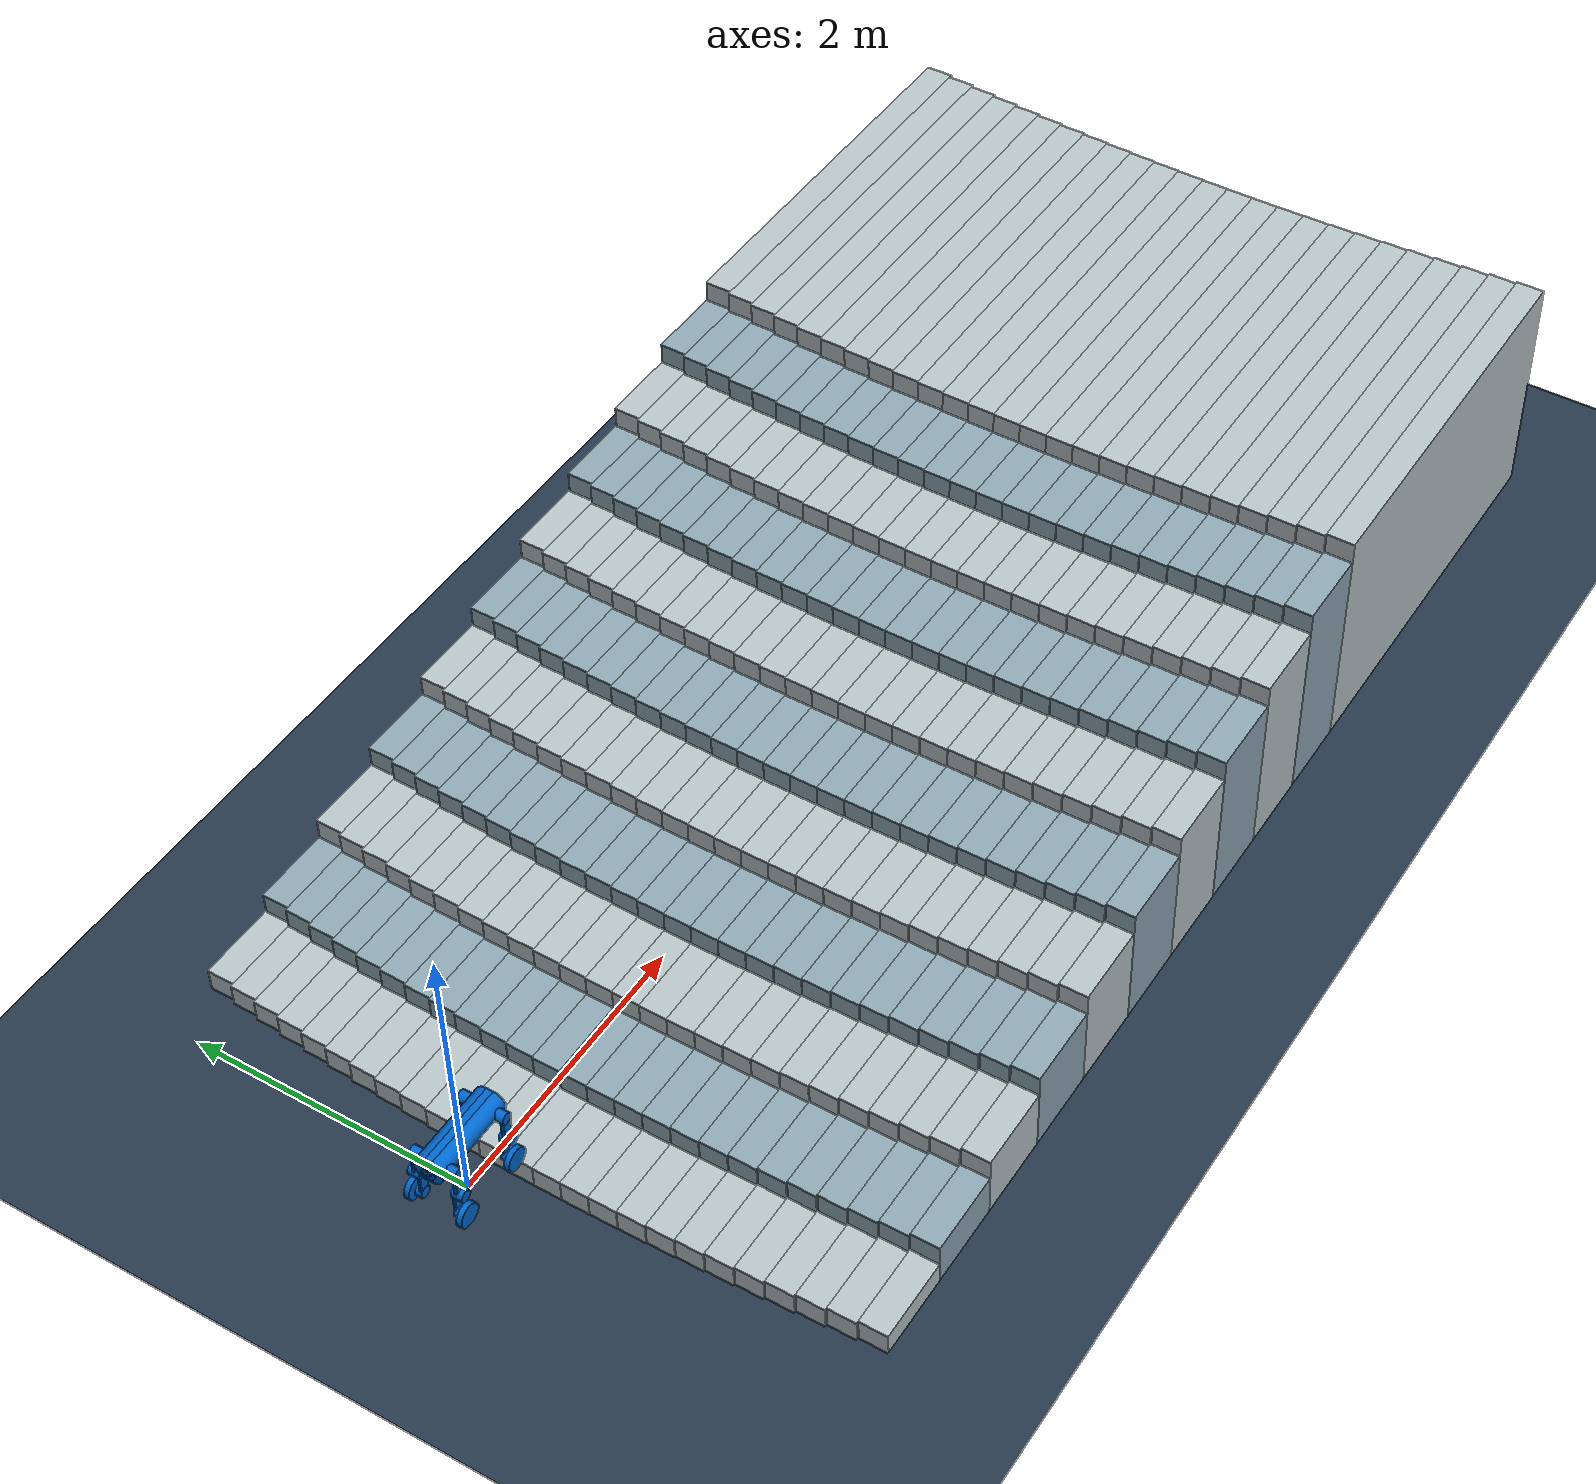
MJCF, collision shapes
<mujoco model="S10">
  <default>
      <default class="robot">
          <default class="motor">
              <joint />
              <motor />
          </default>
          <default class="visual">
              <geom material="default_material" contype="0" conaffinity="0" group="2" />
          </default>
          <default class="collision">
              <geom material="collision_material" condim="3" contype="1" conaffinity="1" solref="0.005 1" friction="1 0.01 0.001" density="0" group="1" />

          </default>
      </default>
  </default>

  <compiler angle="radian" meshdir="D:\Desktop\Code\goai26-s10-racing\upstream\goai_embodied_future_material\src\S10_sdk_deploy\S10_description\s10_mjcf\meshes" />
  <compiler autolimits="true" />

  <asset>
    <material name="default_material" rgba="0.7 0.7 0.7 1" />
    <material name="collision_material" rgba="0.0 0.4 0.8 0.2" />
    <mesh name="base_link" file="base_link.STL" />
    <mesh name="fl_hipx" file="fl_hipx.STL" />
    <mesh name="fl_hipy" file="fl_hipy.STL" />
    <mesh name="fl_knee" file="fl_knee.STL" />
    <mesh name="fl_wheel" file="fl_wheel.STL" />
    <mesh name="fr_hipx" file="fr_hipx.STL" />
    <mesh name="fr_hipy" file="fr_hipy.STL" />
    <mesh name="fr_knee" file="fr_knee.STL" />
    <mesh name="fr_wheel" file="fr_wheel.STL" />
    <mesh name="hl_hipx" file="hl_hipx.STL" />
    <mesh name="hl_hipy" file="hl_hipy.STL" />
    <mesh name="hl_knee" file="hl_knee.STL" />
    <mesh name="hl_wheel" file="hl_wheel.STL" />
    <mesh name="hr_hipx" file="hr_hipx.STL" />
    <mesh name="hr_hipy" file="hr_hipy.STL" />
    <mesh name="hr_knee" file="hr_knee.STL" />
    <mesh name="hr_wheel" file="hr_wheel.STL" />
    <texture name="texplane" type="2d" builtin="checker" rgb1=".2 .3 .4" rgb2=".1 0.15 0.2" width="512" height="512" />

    <material name="MatPlane" reflectance="0.3" texture="texplane" texrepeat="1 1" texuniform="true" />
  </asset>

  <worldbody>

    <light directional="true" pos="-0.5 0.5 3" dir="0 0 -1" />

    <geom name="floor" pos="0 0 -0.43699114824710666" size="100 100 .125" type="plane" material="MatPlane" condim="3" friction="1 0.01 0.01" group="0" />

    <body name="base_link" pos="0 0.0 0.5" quat="1 0 0 0" childclass="robot">
      <freejoint name="floating_base" />
      <inertial pos="-0.000512 0.057317 0.001182" quat="1 0 0 0" mass="8.023087" diaginertia="0.115559 0.171329 0.262028" />
        <site name="imu_site" pos="0.0075 -0.0373 0.0556" size="0.005" rgba="1 0 0 1" />
        <site name="base_site" pos="0 0 0" quat="1 0 0 0" />
      <geom type="mesh" class="visual" mesh="base_link" />
      <geom size="0.08 0.3" pos="0 0.024 0" quat="0.707107 0 0.707107 0" type="cylinder" class="collision" />
      <geom size="0.08 0.3" pos="0 -0.024 0" quat="0.707107 0 0.707107 0" type="cylinder" class="collision" />
      <geom size="0.08 0.024 0.3" quat="0.707107 0 0.707107 0" type="box" class="collision" />
      <body name="fl_hipx" pos="0.2277 0.0574 0">
        <inertial pos="-0.005034 0.023524 4.6e-05" quat="0.25609 0.665262 -0.228203 0.663151" mass="0.627405" diaginertia="0.000415056 0.000391723 0.000223221" />
        <joint name="fl_hipx_joint" pos="0 0 0" axis="-1 0 0" range="-0.6109 0.6109" actuatorfrcrange="-50 50" />
        <geom type="mesh" class="visual" mesh="fl_hipx" />
        <geom size="0.04 0.05" pos="0 0.054 0" quat="0.707107 0.707107 0 0" type="cylinder" class="collision" />
        <body name="fl_hipy" pos="0 0.0779 0">
          <inertial pos="7.4e-05 0.018439 -0.129675" quat="0.701304 -0.0510428 0.0516391 0.709155" mass="0.885874" diaginertia="0.00454086 0.00445199 0.00030515" />
          <joint name="fl_hipy_joint" pos="0 0 0" axis="0 -1 0" range="-2.5307 2.5307" actuatorfrcrange="-50 50" />
          <geom type="mesh" class="visual" mesh="fl_hipy" />
          <geom size="0.032 0.012 0.09" pos="0 0.012 -0.09" type="box" class="collision" />
          <geom size="0.04 0.04" pos="0 0.018 -0.18" quat="0.707107 0.707107 0 0" type="cylinder" class="collision" />
          <body name="fl_knee" pos="0 0 -0.18">
            <inertial pos="-3.2e-05 0.013504 -0.156308" quat="0.703786 -0.068447 0.068447 0.703786" mass="0.640283" diaginertia="0.0022296 0.002221 0.000193398" />
            <joint name="fl_knee_joint" pos="0 0 0" axis="0 -1 0" range="-2.7227 2.7227" actuatorfrcrange="-50 50" />
            <geom type="mesh" class="visual" mesh="fl_knee" />
            <geom size="0.029 0.01 0.09" pos="0 -0.012 -0.09" type="box" class="collision" />
            <geom size="0.04 0.025" pos="0 0.002 -0.18" quat="0.707107 0.707107 0 0" type="cylinder" class="collision" />
            <body name="fl_wheel" pos="0 0.045891 -0.18">
              <inertial pos="-8e-06 0.001694 -5e-06" quat="0.707107 0 0 0.707107" mass="0.587952" diaginertia="0.002003 0.001059 0.001059" />
              <joint name="fl_wheel_joint" pos="0 0 0" axis="0 -1 0" actuatorfrcrange="-14 14" />
              <geom type="mesh" class="visual" mesh="fl_wheel" />
              <geom size="0.081 0.0185" quat="0.707107 0.707107 0 0" type="cylinder" class="collision" />
            </body>
          </body>
        </body>
      </body>
      <body name="fr_hipx" pos="0.2277 -0.0574 0">
        <inertial pos="-0.004831 -0.02349 0.000169" quat="-0.278522 0.675499 0.205833 0.650968" mass="0.626546" diaginertia="0.000415238 0.000395047 0.000218715" />
        <joint name="fr_hipx_joint" pos="0 0 0" axis="-1 0 0" range="-0.6109 0.6109" actuatorfrcrange="-50 50" />
        <geom type="mesh" class="visual" mesh="fr_hipx" />
        <geom size="0.04 0.05" pos="0 -0.054 0" quat="0.707107 0.707107 0 0" type="cylinder" class="collision" />
        <body name="fr_hipy" pos="0 -0.0779 0">
          <inertial pos="-7.4e-05 -0.018439 -0.129675" quat="0.701304 0.0510428 -0.0516391 0.709155" mass="0.885874" diaginertia="0.00454086 0.00445199 0.00030515" />
          <joint name="fr_hipy_joint" pos="0 0 0" axis="0 -1 0" range="-2.5307 2.5307" actuatorfrcrange="-50 50" />
          <geom type="mesh" class="visual" mesh="fr_hipy" />
          <geom size="0.032 0.012 0.09" pos="0 -0.012 -0.09" type="box" class="collision" />
          <geom size="0.04 0.04" pos="0 -0.018 -0.18" quat="0.707107 0.707107 0 0" type="cylinder" class="collision" />
          <body name="fr_knee" pos="0 0 -0.18">
            <inertial pos="3.2e-05 -0.013504 -0.156308" quat="0.703786 0.068447 -0.068447 0.703786" mass="0.640283" diaginertia="0.0022296 0.002221 0.000193398" />
            <joint name="fr_knee_joint" pos="0 0 0" axis="0 -1 0" range="-2.7227 2.7227" actuatorfrcrange="-50 50" />
            <geom type="mesh" class="visual" mesh="fr_knee" />
            <geom size="0.029 0.01 0.09" pos="0 0.012 -0.09" type="box" class="collision" />
            <geom size="0.04 0.025" pos="0 -0.002 -0.18" quat="0.707107 0.707107 0 0" type="cylinder" class="collision" />
            <body name="fr_wheel" pos="0 -0.045891 -0.18">
              <inertial pos="8e-06 -0.001694 5e-06" quat="0.707107 0 0 0.707107" mass="0.587952" diaginertia="0.002003 0.001059 0.001059" />
              <joint name="fr_wheel_joint" pos="0 0 0" axis="0 -1 0" actuatorfrcrange="-14 14" />
              <geom type="mesh" class="visual" mesh="fr_wheel" />
              <geom size="0.081 0.0185" quat="0.707107 0.707107 0 0" type="cylinder" class="collision" />
            </body>
          </body>
        </body>
      </body>
      <body name="hl_hipx" pos="-0.2277 0.0574 0">
        <inertial pos="0.004831 0.02349 0.000169" quat="-0.205833 0.650968 0.278522 0.675499" mass="0.626546" diaginertia="0.000415238 0.000395047 0.000218715" />
        <joint name="hl_hipx_joint" pos="0 0 0" axis="-1 0 0" range="-0.6109 0.6109" actuatorfrcrange="-50 50" />
        <geom type="mesh" class="visual" mesh="hl_hipx" />
        <geom size="0.04 0.05" pos="0 0.054 0" quat="0.707107 0.707107 0 0" type="cylinder" class="collision" />
        <body name="hl_hipy" pos="0 0.0779 0">
          <inertial pos="7.4e-05 0.018439 -0.129675" quat="0.701304 -0.0510428 0.0516391 0.709155" mass="0.885874" diaginertia="0.00454086 0.00445199 0.00030515" />
          <joint name="hl_hipy_joint" pos="0 0 0" axis="0 -1 0" range="-2.5307 2.5307" actuatorfrcrange="-50 50" />
          <geom type="mesh" class="visual" mesh="hl_hipy" />
          <geom size="0.032 0.012 0.09" pos="0 0.012 -0.09" type="box" class="collision" />
          <geom size="0.04 0.04" pos="0 0.018 -0.18" quat="0.707107 0.707107 0 0" type="cylinder" class="collision" />
          <body name="hl_knee" pos="0 0 -0.18">
            <inertial pos="-3.2e-05 0.013504 -0.156308" quat="0.703786 -0.068447 0.068447 0.703786" mass="0.640283" diaginertia="0.0022296 0.002221 0.000193398" />
            <joint name="hl_knee_joint" pos="0 0 0" axis="0 -1 0" range="-2.7227 2.7227" actuatorfrcrange="-50 50" />
            <geom type="mesh" class="visual" mesh="hl_knee" />
            <geom size="0.029 0.01 0.09" pos="0 -0.012 -0.09" type="box" class="collision" />
            <geom size="0.04 0.025" pos="0 0.002 -0.18" quat="0.707107 0.707107 0 0" type="cylinder" class="collision" />
            <body name="hl_wheel" pos="0 0.054891 -0.18">
              <inertial pos="-8e-06 0.001694 -5e-06" quat="0.707107 0 0 0.707107" mass="0.587952" diaginertia="0.002003 0.001059 0.001059" />
              <joint name="hl_wheel_joint" pos="0 0 0" axis="0 -1 0" actuatorfrcrange="-14 14" />
              <geom type="mesh" class="visual" mesh="hl_wheel" />
              <geom size="0.081 0.0185" quat="0.707107 0.707107 0 0" type="cylinder" class="collision" />
            </body>
          </body>
        </body>
      </body>
      <body name="hr_hipx" pos="-0.2277 -0.0574 0">
        <inertial pos="0.005034 -0.023524 4.6e-05" quat="0.228203 0.663151 -0.25609 0.665262" mass="0.627405" diaginertia="0.000415056 0.000391723 0.000223221" />
        <joint name="hr_hipx_joint" pos="0 0 0" axis="-1 0 0" range="-0.6109 0.6109" actuatorfrcrange="-50 50" />
        <geom type="mesh" class="visual" mesh="hr_hipx" />
        <geom size="0.04 0.05" pos="0 -0.054 0" quat="0.707107 0.707107 0 0" type="cylinder" class="collision" />
        <body name="hr_hipy" pos="0 -0.0779 0">
          <inertial pos="-7.4e-05 -0.018439 -0.129675" quat="0.701304 0.0510428 -0.0516391 0.709155" mass="0.885874" diaginertia="0.00454086 0.00445199 0.00030515" />
          <joint name="hr_hipy_joint" pos="0 0 0" axis="0 -1 0" range="-2.5307 2.5307" actuatorfrcrange="-50 50" />
          <geom type="mesh" class="visual" mesh="hr_hipy" />
          <geom size="0.032 0.012 0.09" pos="0 -0.012 -0.09" type="box" class="collision" />
          <geom size="0.04 0.04" pos="0 -0.018 -0.18" quat="0.707107 0.707107 0 0" type="cylinder" class="collision" />
          <body name="hr_knee" pos="0 0 -0.18">
            <inertial pos="3.2e-05 -0.013504 -0.156308" quat="0.703786 0.068447 -0.068447 0.703786" mass="0.640283" diaginertia="0.0022296 0.002221 0.000193398" />
            <joint name="hr_knee_joint" pos="0 0 0" axis="0 -1 0" range="-2.7227 2.7227" actuatorfrcrange="-50 50" />
            <geom type="mesh" class="visual" mesh="hr_knee" />
            <geom size="0.029 0.01 0.09" pos="0 0.012 -0.09" type="box" class="collision" />
            <geom size="0.04 0.025" pos="0 -0.002 -0.18" quat="0.707107 0.707107 0 0" type="cylinder" class="collision" />
            <body name="hr_wheel" pos="0 -0.045891 -0.18">
              <inertial pos="8e-06 -0.001694 5e-06" quat="0.707107 0 0 0.707107" mass="0.587952" diaginertia="0.002003 0.001059 0.001059" />
              <joint name="hr_wheel_joint" pos="0 0 0" axis="0 -1 0" actuatorfrcrange="-14 14" />
              <geom type="mesh" class="visual" mesh="hr_wheel" />
              <geom size="0.081 0.0185" quat="0.707107 0.707107 0 0" type="cylinder" class="collision" />
            </body>
          </body>
        </body>
      </body>
    </body>
  <geom name="step_0_0" type="box" pos="0.8412282365229558 -2.4 -0.4089023267166302" size="0.2847029318569739 0.1 0.12808882153047652" rgba="0.72 0.77 0.78 1" /><geom name="step_0_1" type="box" pos="0.8224118636056439 -2.1999999999999997 -0.4089023267166302" size="0.2847029318569739 0.1 0.12808882153047652" rgba="0.72 0.77 0.78 1" /><geom name="step_0_2" type="box" pos="0.8054584124207806 -1.9999999999999996 -0.4089023267166302" size="0.2847029318569739 0.1 0.12808882153047652" rgba="0.72 0.77 0.78 1" /><geom name="step_0_3" type="box" pos="0.790367882968366 -1.7999999999999994 -0.4089023267166302" size="0.2847029318569739 0.1 0.12808882153047652" rgba="0.72 0.77 0.78 1" /><geom name="step_0_4" type="box" pos="0.7771402752484002 -1.5999999999999992 -0.4089023267166302" size="0.2847029318569739 0.1 0.12808882153047652" rgba="0.72 0.77 0.78 1" /><geom name="step_0_5" type="box" pos="0.7657755892608831 -1.399999999999999 -0.4089023267166302" size="0.2847029318569739 0.1 0.12808882153047652" rgba="0.72 0.77 0.78 1" /><geom name="step_0_6" type="box" pos="0.7562738250058147 -1.1999999999999988 -0.4089023267166302" size="0.2847029318569739 0.1 0.12808882153047652" rgba="0.72 0.77 0.78 1" /><geom name="step_0_7" type="box" pos="0.748634982483195 -0.9999999999999988 -0.4089023267166302" size="0.2847029318569739 0.1 0.12808882153047652" rgba="0.72 0.77 0.78 1" /><geom name="step_0_8" type="box" pos="0.7428590616930241 -0.7999999999999986 -0.4089023267166302" size="0.2847029318569739 0.1 0.12808882153047652" rgba="0.72 0.77 0.78 1" /><geom name="step_0_9" type="box" pos="0.7389460626353017 -0.5999999999999984 -0.4089023267166302" size="0.2847029318569739 0.1 0.12808882153047652" rgba="0.72 0.77 0.78 1" /><geom name="step_0_10" type="box" pos="0.7368959853100283 -0.39999999999999825 -0.4089023267166302" size="0.2847029318569739 0.1 0.12808882153047652" rgba="0.72 0.77 0.78 1" /><geom name="step_0_11" type="box" pos="0.7367088297172033 -0.19999999999999804 -0.4089023267166302" size="0.2847029318569739 0.1 0.12808882153047652" rgba="0.72 0.77 0.78 1" /><geom name="step_0_12" type="box" pos="0.7383845958568274 2.1371793224034263e-15 -0.4089023267166302" size="0.2847029318569739 0.1 0.12808882153047652" rgba="0.72 0.77 0.78 1" /><geom name="step_0_13" type="box" pos="0.7419232837288998 0.20000000000000231 -0.4089023267166302" size="0.2847029318569739 0.1 0.12808882153047652" rgba="0.72 0.77 0.78 1" /><geom name="step_0_14" type="box" pos="0.7473248933334211 0.40000000000000246 -0.4089023267166302" size="0.2847029318569739 0.1 0.12808882153047652" rgba="0.72 0.77 0.78 1" /><geom name="step_0_15" type="box" pos="0.7545894246703913 0.6000000000000026 -0.4089023267166302" size="0.2847029318569739 0.1 0.12808882153047652" rgba="0.72 0.77 0.78 1" /><geom name="step_0_16" type="box" pos="0.7637168777398099 0.8000000000000028 -0.4089023267166302" size="0.2847029318569739 0.1 0.12808882153047652" rgba="0.72 0.77 0.78 1" /><geom name="step_0_17" type="box" pos="0.7747072525416774 1.000000000000003 -0.4089023267166302" size="0.2847029318569739 0.1 0.12808882153047652" rgba="0.72 0.77 0.78 1" /><geom name="step_0_18" type="box" pos="0.7875605490759934 1.2000000000000033 -0.4089023267166302" size="0.2847029318569739 0.1 0.12808882153047652" rgba="0.72 0.77 0.78 1" /><geom name="step_0_19" type="box" pos="0.8022767673427582 1.4000000000000035 -0.4089023267166302" size="0.2847029318569739 0.1 0.12808882153047652" rgba="0.72 0.77 0.78 1" /><geom name="step_0_20" type="box" pos="0.8188559073419719 1.6000000000000036 -0.4089023267166302" size="0.2847029318569739 0.1 0.12808882153047652" rgba="0.72 0.77 0.78 1" /><geom name="step_0_21" type="box" pos="0.8372979690736342 1.8000000000000038 -0.4089023267166302" size="0.2847029318569739 0.1 0.12808882153047652" rgba="0.72 0.77 0.78 1" /><geom name="step_0_22" type="box" pos="0.8576029525377451 2.000000000000004 -0.4089023267166302" size="0.2847029318569739 0.1 0.12808882153047652" rgba="0.72 0.77 0.78 1" /><geom name="step_0_23" type="box" pos="0.8797708577343049 2.200000000000004 -0.4089023267166302" size="0.2847029318569739 0.1 0.12808882153047652" rgba="0.72 0.77 0.78 1" /><geom name="step_0_24" type="box" pos="0.9038016846633132 2.4000000000000044 -0.4089023267166302" size="0.2847029318569739 0.1 0.12808882153047652" rgba="0.72 0.77 0.78 1" /><geom name="step_1_0" type="box" pos="1.4106341002369036 -2.4 -0.33081350518615366" size="0.2847029318569739 0.1 0.20617764306095304" rgba="0.56 0.66 0.71 1" /><geom name="step_1_1" type="box" pos="1.3918177273195917 -2.1999999999999997 -0.33081350518615366" size="0.2847029318569739 0.1 0.20617764306095304" rgba="0.56 0.66 0.71 1" /><geom name="step_1_2" type="box" pos="1.3748642761347283 -1.9999999999999996 -0.33081350518615366" size="0.2847029318569739 0.1 0.20617764306095304" rgba="0.56 0.66 0.71 1" /><geom name="step_1_3" type="box" pos="1.3597737466823139 -1.7999999999999994 -0.33081350518615366" size="0.2847029318569739 0.1 0.20617764306095304" rgba="0.56 0.66 0.71 1" /><geom name="step_1_4" type="box" pos="1.346546138962348 -1.5999999999999992 -0.33081350518615366" size="0.2847029318569739 0.1 0.20617764306095304" rgba="0.56 0.66 0.71 1" /><geom name="step_1_5" type="box" pos="1.335181452974831 -1.399999999999999 -0.33081350518615366" size="0.2847029318569739 0.1 0.20617764306095304" rgba="0.56 0.66 0.71 1" /><geom name="step_1_6" type="box" pos="1.3256796887197626 -1.1999999999999988 -0.33081350518615366" size="0.2847029318569739 0.1 0.20617764306095304" rgba="0.56 0.66 0.71 1" /><geom name="step_1_7" type="box" pos="1.318040846197143 -0.9999999999999988 -0.33081350518615366" size="0.2847029318569739 0.1 0.20617764306095304" rgba="0.56 0.66 0.71 1" /><geom name="step_1_8" type="box" pos="1.3122649254069718 -0.7999999999999986 -0.33081350518615366" size="0.2847029318569739 0.1 0.20617764306095304" rgba="0.56 0.66 0.71 1" /><geom name="step_1_9" type="box" pos="1.3083519263492496 -0.5999999999999984 -0.33081350518615366" size="0.2847029318569739 0.1 0.20617764306095304" rgba="0.56 0.66 0.71 1" /><geom name="step_1_10" type="box" pos="1.3063018490239762 -0.39999999999999825 -0.33081350518615366" size="0.2847029318569739 0.1 0.20617764306095304" rgba="0.56 0.66 0.71 1" /><geom name="step_1_11" type="box" pos="1.3061146934311512 -0.19999999999999804 -0.33081350518615366" size="0.2847029318569739 0.1 0.20617764306095304" rgba="0.56 0.66 0.71 1" /><geom name="step_1_12" type="box" pos="1.307790459570775 2.1371793224034263e-15 -0.33081350518615366" size="0.2847029318569739 0.1 0.20617764306095304" rgba="0.56 0.66 0.71 1" /><geom name="step_1_13" type="box" pos="1.3113291474428475 0.20000000000000231 -0.33081350518615366" size="0.2847029318569739 0.1 0.20617764306095304" rgba="0.56 0.66 0.71 1" /><geom name="step_1_14" type="box" pos="1.316730757047369 0.40000000000000246 -0.33081350518615366" size="0.2847029318569739 0.1 0.20617764306095304" rgba="0.56 0.66 0.71 1" /><geom name="step_1_15" type="box" pos="1.3239952883843389 0.6000000000000026 -0.33081350518615366" size="0.2847029318569739 0.1 0.20617764306095304" rgba="0.56 0.66 0.71 1" /><geom name="step_1_16" type="box" pos="1.3331227414537576 0.8000000000000028 -0.33081350518615366" size="0.2847029318569739 0.1 0.20617764306095304" rgba="0.56 0.66 0.71 1" /><geom name="step_1_17" type="box" pos="1.344113116255625 1.000000000000003 -0.33081350518615366" size="0.2847029318569739 0.1 0.20617764306095304" rgba="0.56 0.66 0.71 1" /><geom name="step_1_18" type="box" pos="1.3569664127899412 1.2000000000000033 -0.33081350518615366" size="0.2847029318569739 0.1 0.20617764306095304" rgba="0.56 0.66 0.71 1" /><geom name="step_1_19" type="box" pos="1.371682631056706 1.4000000000000035 -0.33081350518615366" size="0.2847029318569739 0.1 0.20617764306095304" rgba="0.56 0.66 0.71 1" /><geom name="step_1_20" type="box" pos="1.3882617710559195 1.6000000000000036 -0.33081350518615366" size="0.2847029318569739 0.1 0.20617764306095304" rgba="0.56 0.66 0.71 1" /><geom name="step_1_21" type="box" pos="1.4067038327875818 1.8000000000000038 -0.33081350518615366" size="0.2847029318569739 0.1 0.20617764306095304" rgba="0.56 0.66 0.71 1" /><geom name="step_1_22" type="box" pos="1.427008816251693 2.000000000000004 -0.33081350518615366" size="0.2847029318569739 0.1 0.20617764306095304" rgba="0.56 0.66 0.71 1" /><geom name="step_1_23" type="box" pos="1.4491767214482525 2.200000000000004 -0.33081350518615366" size="0.2847029318569739 0.1 0.20617764306095304" rgba="0.56 0.66 0.71 1" /><geom name="step_1_24" type="box" pos="1.4732075483772609 2.4000000000000044 -0.33081350518615366" size="0.2847029318569739 0.1 0.20617764306095304" rgba="0.56 0.66 0.71 1" /><geom name="step_2_0" type="box" pos="1.9800399639508512 -2.4 -0.25272468365567713" size="0.2847029318569739 0.1 0.28426646459142957" rgba="0.72 0.77 0.78 1" /><geom name="step_2_1" type="box" pos="1.9612235910335392 -2.1999999999999997 -0.25272468365567713" size="0.2847029318569739 0.1 0.28426646459142957" rgba="0.72 0.77 0.78 1" /><geom name="step_2_2" type="box" pos="1.9442701398486761 -1.9999999999999996 -0.25272468365567713" size="0.2847029318569739 0.1 0.28426646459142957" rgba="0.72 0.77 0.78 1" /><geom name="step_2_3" type="box" pos="1.9291796103962615 -1.7999999999999994 -0.25272468365567713" size="0.2847029318569739 0.1 0.28426646459142957" rgba="0.72 0.77 0.78 1" /><geom name="step_2_4" type="box" pos="1.9159520026762957 -1.5999999999999992 -0.25272468365567713" size="0.2847029318569739 0.1 0.28426646459142957" rgba="0.72 0.77 0.78 1" /><geom name="step_2_5" type="box" pos="1.9045873166887786 -1.399999999999999 -0.25272468365567713" size="0.2847029318569739 0.1 0.28426646459142957" rgba="0.72 0.77 0.78 1" /><geom name="step_2_6" type="box" pos="1.8950855524337102 -1.1999999999999988 -0.25272468365567713" size="0.2847029318569739 0.1 0.28426646459142957" rgba="0.72 0.77 0.78 1" /><geom name="step_2_7" type="box" pos="1.8874467099110905 -0.9999999999999988 -0.25272468365567713" size="0.2847029318569739 0.1 0.28426646459142957" rgba="0.72 0.77 0.78 1" /><geom name="step_2_8" type="box" pos="1.8816707891209195 -0.7999999999999986 -0.25272468365567713" size="0.2847029318569739 0.1 0.28426646459142957" rgba="0.72 0.77 0.78 1" /><geom name="step_2_9" type="box" pos="1.8777577900631972 -0.5999999999999984 -0.25272468365567713" size="0.2847029318569739 0.1 0.28426646459142957" rgba="0.72 0.77 0.78 1" /><geom name="step_2_10" type="box" pos="1.8757077127379238 -0.39999999999999825 -0.25272468365567713" size="0.2847029318569739 0.1 0.28426646459142957" rgba="0.72 0.77 0.78 1" /><geom name="step_2_11" type="box" pos="1.8755205571450988 -0.19999999999999804 -0.25272468365567713" size="0.2847029318569739 0.1 0.28426646459142957" rgba="0.72 0.77 0.78 1" /><geom name="step_2_12" type="box" pos="1.8771963232847226 2.1371793224034263e-15 -0.25272468365567713" size="0.2847029318569739 0.1 0.28426646459142957" rgba="0.72 0.77 0.78 1" /><geom name="step_2_13" type="box" pos="1.880735011156795 0.20000000000000231 -0.25272468365567713" size="0.2847029318569739 0.1 0.28426646459142957" rgba="0.72 0.77 0.78 1" /><geom name="step_2_14" type="box" pos="1.8861366207613166 0.40000000000000246 -0.25272468365567713" size="0.2847029318569739 0.1 0.28426646459142957" rgba="0.72 0.77 0.78 1" /><geom name="step_2_15" type="box" pos="1.8934011520982865 0.6000000000000026 -0.25272468365567713" size="0.2847029318569739 0.1 0.28426646459142957" rgba="0.72 0.77 0.78 1" /><geom name="step_2_16" type="box" pos="1.9025286051677053 0.8000000000000028 -0.25272468365567713" size="0.2847029318569739 0.1 0.28426646459142957" rgba="0.72 0.77 0.78 1" /><geom name="step_2_17" type="box" pos="1.9135189799695727 1.000000000000003 -0.25272468365567713" size="0.2847029318569739 0.1 0.28426646459142957" rgba="0.72 0.77 0.78 1" /><geom name="step_2_18" type="box" pos="1.9263722765038889 1.2000000000000033 -0.25272468365567713" size="0.2847029318569739 0.1 0.28426646459142957" rgba="0.72 0.77 0.78 1" /><geom name="step_2_19" type="box" pos="1.9410884947706537 1.4000000000000035 -0.25272468365567713" size="0.2847029318569739 0.1 0.28426646459142957" rgba="0.72 0.77 0.78 1" /><geom name="step_2_20" type="box" pos="1.9576676347698672 1.6000000000000036 -0.25272468365567713" size="0.2847029318569739 0.1 0.28426646459142957" rgba="0.72 0.77 0.78 1" /><geom name="step_2_21" type="box" pos="1.9761096965015295 1.8000000000000038 -0.25272468365567713" size="0.2847029318569739 0.1 0.28426646459142957" rgba="0.72 0.77 0.78 1" /><geom name="step_2_22" type="box" pos="1.9964146799656406 2.000000000000004 -0.25272468365567713" size="0.2847029318569739 0.1 0.28426646459142957" rgba="0.72 0.77 0.78 1" /><geom name="step_2_23" type="box" pos="2.0185825851622003 2.200000000000004 -0.25272468365567713" size="0.2847029318569739 0.1 0.28426646459142957" rgba="0.72 0.77 0.78 1" /><geom name="step_2_24" type="box" pos="2.0426134120912085 2.4000000000000044 -0.25272468365567713" size="0.2847029318569739 0.1 0.28426646459142957" rgba="0.72 0.77 0.78 1" /><geom name="step_3_0" type="box" pos="2.5494458276647993 -2.4 -0.17463586212520063" size="0.2847029318569739 0.1 0.36235528612190604" rgba="0.56 0.66 0.71 1" /><geom name="step_3_1" type="box" pos="2.5306294547474875 -2.1999999999999997 -0.17463586212520063" size="0.2847029318569739 0.1 0.36235528612190604" rgba="0.56 0.66 0.71 1" /><geom name="step_3_2" type="box" pos="2.513676003562624 -1.9999999999999996 -0.17463586212520063" size="0.2847029318569739 0.1 0.36235528612190604" rgba="0.56 0.66 0.71 1" /><geom name="step_3_3" type="box" pos="2.4985854741102096 -1.7999999999999994 -0.17463586212520063" size="0.2847029318569739 0.1 0.36235528612190604" rgba="0.56 0.66 0.71 1" /><geom name="step_3_4" type="box" pos="2.4853578663902436 -1.5999999999999992 -0.17463586212520063" size="0.2847029318569739 0.1 0.36235528612190604" rgba="0.56 0.66 0.71 1" /><geom name="step_3_5" type="box" pos="2.4739931804027266 -1.399999999999999 -0.17463586212520063" size="0.2847029318569739 0.1 0.36235528612190604" rgba="0.56 0.66 0.71 1" /><geom name="step_3_6" type="box" pos="2.464491416147658 -1.1999999999999988 -0.17463586212520063" size="0.2847029318569739 0.1 0.36235528612190604" rgba="0.56 0.66 0.71 1" /><geom name="step_3_7" type="box" pos="2.456852573625038 -0.9999999999999988 -0.17463586212520063" size="0.2847029318569739 0.1 0.36235528612190604" rgba="0.56 0.66 0.71 1" /><geom name="step_3_8" type="box" pos="2.4510766528348675 -0.7999999999999986 -0.17463586212520063" size="0.2847029318569739 0.1 0.36235528612190604" rgba="0.56 0.66 0.71 1" /><geom name="step_3_9" type="box" pos="2.4471636537771455 -0.5999999999999984 -0.17463586212520063" size="0.2847029318569739 0.1 0.36235528612190604" rgba="0.56 0.66 0.71 1" /><geom name="step_3_10" type="box" pos="2.4451135764518717 -0.39999999999999825 -0.17463586212520063" size="0.2847029318569739 0.1 0.36235528612190604" rgba="0.56 0.66 0.71 1" /><geom name="step_3_11" type="box" pos="2.444926420859047 -0.19999999999999804 -0.17463586212520063" size="0.2847029318569739 0.1 0.36235528612190604" rgba="0.56 0.66 0.71 1" /><geom name="step_3_12" type="box" pos="2.4466021869986707 2.1371793224034263e-15 -0.17463586212520063" size="0.2847029318569739 0.1 0.36235528612190604" rgba="0.56 0.66 0.71 1" /><geom name="step_3_13" type="box" pos="2.450140874870743 0.20000000000000231 -0.17463586212520063" size="0.2847029318569739 0.1 0.36235528612190604" rgba="0.56 0.66 0.71 1" /><geom name="step_3_14" type="box" pos="2.4555424844752647 0.40000000000000246 -0.17463586212520063" size="0.2847029318569739 0.1 0.36235528612190604" rgba="0.56 0.66 0.71 1" /><geom name="step_3_15" type="box" pos="2.4628070158122344 0.6000000000000026 -0.17463586212520063" size="0.2847029318569739 0.1 0.36235528612190604" rgba="0.56 0.66 0.71 1" /><geom name="step_3_16" type="box" pos="2.4719344688816536 0.8000000000000028 -0.17463586212520063" size="0.2847029318569739 0.1 0.36235528612190604" rgba="0.56 0.66 0.71 1" /><geom name="step_3_17" type="box" pos="2.482924843683521 1.000000000000003 -0.17463586212520063" size="0.2847029318569739 0.1 0.36235528612190604" rgba="0.56 0.66 0.71 1" /><geom name="step_3_18" type="box" pos="2.495778140217837 1.2000000000000033 -0.17463586212520063" size="0.2847029318569739 0.1 0.36235528612190604" rgba="0.56 0.66 0.71 1" /><geom name="step_3_19" type="box" pos="2.5104943584846016 1.4000000000000035 -0.17463586212520063" size="0.2847029318569739 0.1 0.36235528612190604" rgba="0.56 0.66 0.71 1" /><geom name="step_3_20" type="box" pos="2.5270734984838152 1.6000000000000036 -0.17463586212520063" size="0.2847029318569739 0.1 0.36235528612190604" rgba="0.56 0.66 0.71 1" /><geom name="step_3_21" type="box" pos="2.5455155602154775 1.8000000000000038 -0.17463586212520063" size="0.2847029318569739 0.1 0.36235528612190604" rgba="0.56 0.66 0.71 1" /><geom name="step_3_22" type="box" pos="2.5658205436795885 2.000000000000004 -0.17463586212520063" size="0.2847029318569739 0.1 0.36235528612190604" rgba="0.56 0.66 0.71 1" /><geom name="step_3_23" type="box" pos="2.587988448876148 2.200000000000004 -0.17463586212520063" size="0.2847029318569739 0.1 0.36235528612190604" rgba="0.56 0.66 0.71 1" /><geom name="step_3_24" type="box" pos="2.612019275805157 2.4000000000000044 -0.17463586212520063" size="0.2847029318569739 0.1 0.36235528612190604" rgba="0.56 0.66 0.71 1" /><geom name="step_4_0" type="box" pos="3.118851691378747 -2.4 -0.0965470405947241" size="0.2847029318569739 0.1 0.4404441076523826" rgba="0.72 0.77 0.78 1" /><geom name="step_4_1" type="box" pos="3.100035318461435 -2.1999999999999997 -0.0965470405947241" size="0.2847029318569739 0.1 0.4404441076523826" rgba="0.72 0.77 0.78 1" /><geom name="step_4_2" type="box" pos="3.083081867276572 -1.9999999999999996 -0.0965470405947241" size="0.2847029318569739 0.1 0.4404441076523826" rgba="0.72 0.77 0.78 1" /><geom name="step_4_3" type="box" pos="3.0679913378241572 -1.7999999999999994 -0.0965470405947241" size="0.2847029318569739 0.1 0.4404441076523826" rgba="0.72 0.77 0.78 1" /><geom name="step_4_4" type="box" pos="3.054763730104191 -1.5999999999999992 -0.0965470405947241" size="0.2847029318569739 0.1 0.4404441076523826" rgba="0.72 0.77 0.78 1" /><geom name="step_4_5" type="box" pos="3.0433990441166743 -1.399999999999999 -0.0965470405947241" size="0.2847029318569739 0.1 0.4404441076523826" rgba="0.72 0.77 0.78 1" /><geom name="step_4_6" type="box" pos="3.0338972798616055 -1.1999999999999988 -0.0965470405947241" size="0.2847029318569739 0.1 0.4404441076523826" rgba="0.72 0.77 0.78 1" /><geom name="step_4_7" type="box" pos="3.026258437338986 -0.9999999999999988 -0.0965470405947241" size="0.2847029318569739 0.1 0.4404441076523826" rgba="0.72 0.77 0.78 1" /><geom name="step_4_8" type="box" pos="3.020482516548815 -0.7999999999999986 -0.0965470405947241" size="0.2847029318569739 0.1 0.4404441076523826" rgba="0.72 0.77 0.78 1" /><geom name="step_4_9" type="box" pos="3.016569517491093 -0.5999999999999984 -0.0965470405947241" size="0.2847029318569739 0.1 0.4404441076523826" rgba="0.72 0.77 0.78 1" /><geom name="step_4_10" type="box" pos="3.0145194401658193 -0.39999999999999825 -0.0965470405947241" size="0.2847029318569739 0.1 0.4404441076523826" rgba="0.72 0.77 0.78 1" /><geom name="step_4_11" type="box" pos="3.0143322845729945 -0.19999999999999804 -0.0965470405947241" size="0.2847029318569739 0.1 0.4404441076523826" rgba="0.72 0.77 0.78 1" /><geom name="step_4_12" type="box" pos="3.0160080507126183 2.1371793224034263e-15 -0.0965470405947241" size="0.2847029318569739 0.1 0.4404441076523826" rgba="0.72 0.77 0.78 1" /><geom name="step_4_13" type="box" pos="3.019546738584691 0.20000000000000231 -0.0965470405947241" size="0.2847029318569739 0.1 0.4404441076523826" rgba="0.72 0.77 0.78 1" /><geom name="step_4_14" type="box" pos="3.0249483481892123 0.40000000000000246 -0.0965470405947241" size="0.2847029318569739 0.1 0.4404441076523826" rgba="0.72 0.77 0.78 1" /><geom name="step_4_15" type="box" pos="3.032212879526182 0.6000000000000026 -0.0965470405947241" size="0.2847029318569739 0.1 0.4404441076523826" rgba="0.72 0.77 0.78 1" /><geom name="step_4_16" type="box" pos="3.041340332595601 0.8000000000000028 -0.0965470405947241" size="0.2847029318569739 0.1 0.4404441076523826" rgba="0.72 0.77 0.78 1" /><geom name="step_4_17" type="box" pos="3.0523307073974686 1.000000000000003 -0.0965470405947241" size="0.2847029318569739 0.1 0.4404441076523826" rgba="0.72 0.77 0.78 1" /><geom name="step_4_18" type="box" pos="3.0651840039317846 1.2000000000000033 -0.0965470405947241" size="0.2847029318569739 0.1 0.4404441076523826" rgba="0.72 0.77 0.78 1" /><geom name="step_4_19" type="box" pos="3.079900222198549 1.4000000000000035 -0.0965470405947241" size="0.2847029318569739 0.1 0.4404441076523826" rgba="0.72 0.77 0.78 1" /><geom name="step_4_20" type="box" pos="3.096479362197763 1.6000000000000036 -0.0965470405947241" size="0.2847029318569739 0.1 0.4404441076523826" rgba="0.72 0.77 0.78 1" /><geom name="step_4_21" type="box" pos="3.114921423929425 1.8000000000000038 -0.0965470405947241" size="0.2847029318569739 0.1 0.4404441076523826" rgba="0.72 0.77 0.78 1" /><geom name="step_4_22" type="box" pos="3.135226407393536 2.000000000000004 -0.0965470405947241" size="0.2847029318569739 0.1 0.4404441076523826" rgba="0.72 0.77 0.78 1" /><geom name="step_4_23" type="box" pos="3.1573943125900956 2.200000000000004 -0.0965470405947241" size="0.2847029318569739 0.1 0.4404441076523826" rgba="0.72 0.77 0.78 1" /><geom name="step_4_24" type="box" pos="3.1814251395191047 2.4000000000000044 -0.0965470405947241" size="0.2847029318569739 0.1 0.4404441076523826" rgba="0.72 0.77 0.78 1" /><geom name="step_5_0" type="box" pos="3.6882575550926946 -2.4 -0.01845821906424766" size="0.2847029318569739 0.1 0.5185329291828591" rgba="0.56 0.66 0.71 1" /><geom name="step_5_1" type="box" pos="3.6694411821753827 -2.1999999999999997 -0.01845821906424766" size="0.2847029318569739 0.1 0.5185329291828591" rgba="0.56 0.66 0.71 1" /><geom name="step_5_2" type="box" pos="3.6524877309905195 -1.9999999999999996 -0.01845821906424766" size="0.2847029318569739 0.1 0.5185329291828591" rgba="0.56 0.66 0.71 1" /><geom name="step_5_3" type="box" pos="3.637397201538105 -1.7999999999999994 -0.01845821906424766" size="0.2847029318569739 0.1 0.5185329291828591" rgba="0.56 0.66 0.71 1" /><geom name="step_5_4" type="box" pos="3.624169593818139 -1.5999999999999992 -0.01845821906424766" size="0.2847029318569739 0.1 0.5185329291828591" rgba="0.56 0.66 0.71 1" /><geom name="step_5_5" type="box" pos="3.612804907830622 -1.399999999999999 -0.01845821906424766" size="0.2847029318569739 0.1 0.5185329291828591" rgba="0.56 0.66 0.71 1" /><geom name="step_5_6" type="box" pos="3.603303143575553 -1.1999999999999988 -0.01845821906424766" size="0.2847029318569739 0.1 0.5185329291828591" rgba="0.56 0.66 0.71 1" /><geom name="step_5_7" type="box" pos="3.5956643010529334 -0.9999999999999988 -0.01845821906424766" size="0.2847029318569739 0.1 0.5185329291828591" rgba="0.56 0.66 0.71 1" /><geom name="step_5_8" type="box" pos="3.589888380262763 -0.7999999999999986 -0.01845821906424766" size="0.2847029318569739 0.1 0.5185329291828591" rgba="0.56 0.66 0.71 1" /><geom name="step_5_9" type="box" pos="3.585975381205041 -0.5999999999999984 -0.01845821906424766" size="0.2847029318569739 0.1 0.5185329291828591" rgba="0.56 0.66 0.71 1" /><geom name="step_5_10" type="box" pos="3.583925303879767 -0.39999999999999825 -0.01845821906424766" size="0.2847029318569739 0.1 0.5185329291828591" rgba="0.56 0.66 0.71 1" /><geom name="step_5_11" type="box" pos="3.583738148286942 -0.19999999999999804 -0.01845821906424766" size="0.2847029318569739 0.1 0.5185329291828591" rgba="0.56 0.66 0.71 1" /><geom name="step_5_12" type="box" pos="3.585413914426566 2.1371793224034263e-15 -0.01845821906424766" size="0.2847029318569739 0.1 0.5185329291828591" rgba="0.56 0.66 0.71 1" /><geom name="step_5_13" type="box" pos="3.5889526022986384 0.20000000000000231 -0.01845821906424766" size="0.2847029318569739 0.1 0.5185329291828591" rgba="0.56 0.66 0.71 1" /><geom name="step_5_14" type="box" pos="3.59435421190316 0.40000000000000246 -0.01845821906424766" size="0.2847029318569739 0.1 0.5185329291828591" rgba="0.56 0.66 0.71 1" /><geom name="step_5_15" type="box" pos="3.6016187432401296 0.6000000000000026 -0.01845821906424766" size="0.2847029318569739 0.1 0.5185329291828591" rgba="0.56 0.66 0.71 1" /><geom name="step_5_16" type="box" pos="3.610746196309549 0.8000000000000028 -0.01845821906424766" size="0.2847029318569739 0.1 0.5185329291828591" rgba="0.56 0.66 0.71 1" /><geom name="step_5_17" type="box" pos="3.6217365711114162 1.000000000000003 -0.01845821906424766" size="0.2847029318569739 0.1 0.5185329291828591" rgba="0.56 0.66 0.71 1" /><geom name="step_5_18" type="box" pos="3.634589867645732 1.2000000000000033 -0.01845821906424766" size="0.2847029318569739 0.1 0.5185329291828591" rgba="0.56 0.66 0.71 1" /><geom name="step_5_19" type="box" pos="3.649306085912497 1.4000000000000035 -0.01845821906424766" size="0.2847029318569739 0.1 0.5185329291828591" rgba="0.56 0.66 0.71 1" /><geom name="step_5_20" type="box" pos="3.6658852259117105 1.6000000000000036 -0.01845821906424766" size="0.2847029318569739 0.1 0.5185329291828591" rgba="0.56 0.66 0.71 1" /><geom name="step_5_21" type="box" pos="3.684327287643373 1.8000000000000038 -0.01845821906424766" size="0.2847029318569739 0.1 0.5185329291828591" rgba="0.56 0.66 0.71 1" /><geom name="step_5_22" type="box" pos="3.7046322711074837 2.000000000000004 -0.01845821906424766" size="0.2847029318569739 0.1 0.5185329291828591" rgba="0.56 0.66 0.71 1" /><geom name="step_5_23" type="box" pos="3.7268001763040433 2.200000000000004 -0.01845821906424766" size="0.2847029318569739 0.1 0.5185329291828591" rgba="0.56 0.66 0.71 1" /><geom name="step_5_24" type="box" pos="3.7508310032330523 2.4000000000000044 -0.01845821906424766" size="0.2847029318569739 0.1 0.5185329291828591" rgba="0.56 0.66 0.71 1" /><geom name="step_6_0" type="box" pos="4.257663418806643 -2.4 0.05963060246622892" size="0.2847029318569739 0.1 0.5966217507133356" rgba="0.72 0.77 0.78 1" /><geom name="step_6_1" type="box" pos="4.23884704588933 -2.1999999999999997 0.05963060246622892" size="0.2847029318569739 0.1 0.5966217507133356" rgba="0.72 0.77 0.78 1" /><geom name="step_6_2" type="box" pos="4.221893594704468 -1.9999999999999996 0.05963060246622892" size="0.2847029318569739 0.1 0.5966217507133356" rgba="0.72 0.77 0.78 1" /><geom name="step_6_3" type="box" pos="4.2068030652520525 -1.7999999999999994 0.05963060246622892" size="0.2847029318569739 0.1 0.5966217507133356" rgba="0.72 0.77 0.78 1" /><geom name="step_6_4" type="box" pos="4.193575457532087 -1.5999999999999992 0.05963060246622892" size="0.2847029318569739 0.1 0.5966217507133356" rgba="0.72 0.77 0.78 1" /><geom name="step_6_5" type="box" pos="4.18221077154457 -1.399999999999999 0.05963060246622892" size="0.2847029318569739 0.1 0.5966217507133356" rgba="0.72 0.77 0.78 1" /><geom name="step_6_6" type="box" pos="4.172709007289501 -1.1999999999999988 0.05963060246622892" size="0.2847029318569739 0.1 0.5966217507133356" rgba="0.72 0.77 0.78 1" /><geom name="step_6_7" type="box" pos="4.165070164766881 -0.9999999999999988 0.05963060246622892" size="0.2847029318569739 0.1 0.5966217507133356" rgba="0.72 0.77 0.78 1" /><geom name="step_6_8" type="box" pos="4.159294243976711 -0.7999999999999986 0.05963060246622892" size="0.2847029318569739 0.1 0.5966217507133356" rgba="0.72 0.77 0.78 1" /><geom name="step_6_9" type="box" pos="4.155381244918988 -0.5999999999999984 0.05963060246622892" size="0.2847029318569739 0.1 0.5966217507133356" rgba="0.72 0.77 0.78 1" /><geom name="step_6_10" type="box" pos="4.153331167593715 -0.39999999999999825 0.05963060246622892" size="0.2847029318569739 0.1 0.5966217507133356" rgba="0.72 0.77 0.78 1" /><geom name="step_6_11" type="box" pos="4.15314401200089 -0.19999999999999804 0.05963060246622892" size="0.2847029318569739 0.1 0.5966217507133356" rgba="0.72 0.77 0.78 1" /><geom name="step_6_12" type="box" pos="4.154819778140514 2.1371793224034263e-15 0.05963060246622892" size="0.2847029318569739 0.1 0.5966217507133356" rgba="0.72 0.77 0.78 1" /><geom name="step_6_13" type="box" pos="4.1583584660125865 0.20000000000000231 0.05963060246622892" size="0.2847029318569739 0.1 0.5966217507133356" rgba="0.72 0.77 0.78 1" /><geom name="step_6_14" type="box" pos="4.163760075617108 0.40000000000000246 0.05963060246622892" size="0.2847029318569739 0.1 0.5966217507133356" rgba="0.72 0.77 0.78 1" /><geom name="step_6_15" type="box" pos="4.171024606954077 0.6000000000000026 0.05963060246622892" size="0.2847029318569739 0.1 0.5966217507133356" rgba="0.72 0.77 0.78 1" /><geom name="step_6_16" type="box" pos="4.180152060023497 0.8000000000000028 0.05963060246622892" size="0.2847029318569739 0.1 0.5966217507133356" rgba="0.72 0.77 0.78 1" /><geom name="step_6_17" type="box" pos="4.191142434825364 1.000000000000003 0.05963060246622892" size="0.2847029318569739 0.1 0.5966217507133356" rgba="0.72 0.77 0.78 1" /><geom name="step_6_18" type="box" pos="4.20399573135968 1.2000000000000033 0.05963060246622892" size="0.2847029318569739 0.1 0.5966217507133356" rgba="0.72 0.77 0.78 1" /><geom name="step_6_19" type="box" pos="4.218711949626445 1.4000000000000035 0.05963060246622892" size="0.2847029318569739 0.1 0.5966217507133356" rgba="0.72 0.77 0.78 1" /><geom name="step_6_20" type="box" pos="4.235291089625658 1.6000000000000036 0.05963060246622892" size="0.2847029318569739 0.1 0.5966217507133356" rgba="0.72 0.77 0.78 1" /><geom name="step_6_21" type="box" pos="4.253733151357321 1.8000000000000038 0.05963060246622892" size="0.2847029318569739 0.1 0.5966217507133356" rgba="0.72 0.77 0.78 1" /><geom name="step_6_22" type="box" pos="4.274038134821431 2.000000000000004 0.05963060246622892" size="0.2847029318569739 0.1 0.5966217507133356" rgba="0.72 0.77 0.78 1" /><geom name="step_6_23" type="box" pos="4.296206040017991 2.200000000000004 0.05963060246622892" size="0.2847029318569739 0.1 0.5966217507133356" rgba="0.72 0.77 0.78 1" /><geom name="step_6_24" type="box" pos="4.320236866947 2.4000000000000044 0.05963060246622892" size="0.2847029318569739 0.1 0.5966217507133356" rgba="0.72 0.77 0.78 1" /><geom name="step_7_0" type="box" pos="4.82706928252059 -2.4 0.1377194239967054" size="0.2847029318569739 0.1 0.674710572243812" rgba="0.56 0.66 0.71 1" /><geom name="step_7_1" type="box" pos="4.8082529096032784 -2.1999999999999997 0.1377194239967054" size="0.2847029318569739 0.1 0.674710572243812" rgba="0.56 0.66 0.71 1" /><geom name="step_7_2" type="box" pos="4.791299458418415 -1.9999999999999996 0.1377194239967054" size="0.2847029318569739 0.1 0.674710572243812" rgba="0.56 0.66 0.71 1" /><geom name="step_7_3" type="box" pos="4.776208928966001 -1.7999999999999994 0.1377194239967054" size="0.2847029318569739 0.1 0.674710572243812" rgba="0.56 0.66 0.71 1" /><geom name="step_7_4" type="box" pos="4.762981321246035 -1.5999999999999992 0.1377194239967054" size="0.2847029318569739 0.1 0.674710572243812" rgba="0.56 0.66 0.71 1" /><geom name="step_7_5" type="box" pos="4.751616635258518 -1.399999999999999 0.1377194239967054" size="0.2847029318569739 0.1 0.674710572243812" rgba="0.56 0.66 0.71 1" /><geom name="step_7_6" type="box" pos="4.74211487100345 -1.1999999999999988 0.1377194239967054" size="0.2847029318569739 0.1 0.674710572243812" rgba="0.56 0.66 0.71 1" /><geom name="step_7_7" type="box" pos="4.73447602848083 -0.9999999999999988 0.1377194239967054" size="0.2847029318569739 0.1 0.674710572243812" rgba="0.56 0.66 0.71 1" /><geom name="step_7_8" type="box" pos="4.728700107690659 -0.7999999999999986 0.1377194239967054" size="0.2847029318569739 0.1 0.674710572243812" rgba="0.56 0.66 0.71 1" /><geom name="step_7_9" type="box" pos="4.7247871086329365 -0.5999999999999984 0.1377194239967054" size="0.2847029318569739 0.1 0.674710572243812" rgba="0.56 0.66 0.71 1" /><geom name="step_7_10" type="box" pos="4.722737031307663 -0.39999999999999825 0.1377194239967054" size="0.2847029318569739 0.1 0.674710572243812" rgba="0.56 0.66 0.71 1" /><geom name="step_7_11" type="box" pos="4.722549875714838 -0.19999999999999804 0.1377194239967054" size="0.2847029318569739 0.1 0.674710572243812" rgba="0.56 0.66 0.71 1" /><geom name="step_7_12" type="box" pos="4.724225641854462 2.1371793224034263e-15 0.1377194239967054" size="0.2847029318569739 0.1 0.674710572243812" rgba="0.56 0.66 0.71 1" /><geom name="step_7_13" type="box" pos="4.727764329726535 0.20000000000000231 0.1377194239967054" size="0.2847029318569739 0.1 0.674710572243812" rgba="0.56 0.66 0.71 1" /><geom name="step_7_14" type="box" pos="4.733165939331055 0.40000000000000246 0.1377194239967054" size="0.2847029318569739 0.1 0.674710572243812" rgba="0.56 0.66 0.71 1" /><geom name="step_7_15" type="box" pos="4.740430470668025 0.6000000000000026 0.1377194239967054" size="0.2847029318569739 0.1 0.674710572243812" rgba="0.56 0.66 0.71 1" /><geom name="step_7_16" type="box" pos="4.749557923737444 0.8000000000000028 0.1377194239967054" size="0.2847029318569739 0.1 0.674710572243812" rgba="0.56 0.66 0.71 1" /><geom name="step_7_17" type="box" pos="4.7605482985393115 1.000000000000003 0.1377194239967054" size="0.2847029318569739 0.1 0.674710572243812" rgba="0.56 0.66 0.71 1" /><geom name="step_7_18" type="box" pos="4.7734015950736275 1.2000000000000033 0.1377194239967054" size="0.2847029318569739 0.1 0.674710572243812" rgba="0.56 0.66 0.71 1" /><geom name="step_7_19" type="box" pos="4.788117813340392 1.4000000000000035 0.1377194239967054" size="0.2847029318569739 0.1 0.674710572243812" rgba="0.56 0.66 0.71 1" /><geom name="step_7_20" type="box" pos="4.804696953339607 1.6000000000000036 0.1377194239967054" size="0.2847029318569739 0.1 0.674710572243812" rgba="0.56 0.66 0.71 1" /><geom name="step_7_21" type="box" pos="4.823139015071269 1.8000000000000038 0.1377194239967054" size="0.2847029318569739 0.1 0.674710572243812" rgba="0.56 0.66 0.71 1" /><geom name="step_7_22" type="box" pos="4.843443998535379 2.000000000000004 0.1377194239967054" size="0.2847029318569739 0.1 0.674710572243812" rgba="0.56 0.66 0.71 1" /><geom name="step_7_23" type="box" pos="4.865611903731939 2.200000000000004 0.1377194239967054" size="0.2847029318569739 0.1 0.674710572243812" rgba="0.56 0.66 0.71 1" /><geom name="step_7_24" type="box" pos="4.889642730660948 2.4000000000000044 0.1377194239967054" size="0.2847029318569739 0.1 0.674710572243812" rgba="0.56 0.66 0.71 1" /><geom name="step_8_0" type="box" pos="5.396475146234538 -2.4 0.21580824552718186" size="0.2847029318569739 0.1 0.7527993937742885" rgba="0.72 0.77 0.78 1" /><geom name="step_8_1" type="box" pos="5.3776587733172265 -2.1999999999999997 0.21580824552718186" size="0.2847029318569739 0.1 0.7527993937742885" rgba="0.72 0.77 0.78 1" /><geom name="step_8_2" type="box" pos="5.360705322132363 -1.9999999999999996 0.21580824552718186" size="0.2847029318569739 0.1 0.7527993937742885" rgba="0.72 0.77 0.78 1" /><geom name="step_8_3" type="box" pos="5.345614792679949 -1.7999999999999994 0.21580824552718186" size="0.2847029318569739 0.1 0.7527993937742885" rgba="0.72 0.77 0.78 1" /><geom name="step_8_4" type="box" pos="5.332387184959983 -1.5999999999999992 0.21580824552718186" size="0.2847029318569739 0.1 0.7527993937742885" rgba="0.72 0.77 0.78 1" /><geom name="step_8_5" type="box" pos="5.321022498972466 -1.399999999999999 0.21580824552718186" size="0.2847029318569739 0.1 0.7527993937742885" rgba="0.72 0.77 0.78 1" /><geom name="step_8_6" type="box" pos="5.311520734717398 -1.1999999999999988 0.21580824552718186" size="0.2847029318569739 0.1 0.7527993937742885" rgba="0.72 0.77 0.78 1" /><geom name="step_8_7" type="box" pos="5.303881892194778 -0.9999999999999988 0.21580824552718186" size="0.2847029318569739 0.1 0.7527993937742885" rgba="0.72 0.77 0.78 1" /><geom name="step_8_8" type="box" pos="5.298105971404607 -0.7999999999999986 0.21580824552718186" size="0.2847029318569739 0.1 0.7527993937742885" rgba="0.72 0.77 0.78 1" /><geom name="step_8_9" type="box" pos="5.294192972346885 -0.5999999999999984 0.21580824552718186" size="0.2847029318569739 0.1 0.7527993937742885" rgba="0.72 0.77 0.78 1" /><geom name="step_8_10" type="box" pos="5.292142895021611 -0.39999999999999825 0.21580824552718186" size="0.2847029318569739 0.1 0.7527993937742885" rgba="0.72 0.77 0.78 1" /><geom name="step_8_11" type="box" pos="5.291955739428786 -0.19999999999999804 0.21580824552718186" size="0.2847029318569739 0.1 0.7527993937742885" rgba="0.72 0.77 0.78 1" /><geom name="step_8_12" type="box" pos="5.29363150556841 2.1371793224034263e-15 0.21580824552718186" size="0.2847029318569739 0.1 0.7527993937742885" rgba="0.72 0.77 0.78 1" /><geom name="step_8_13" type="box" pos="5.297170193440483 0.20000000000000231 0.21580824552718186" size="0.2847029318569739 0.1 0.7527993937742885" rgba="0.72 0.77 0.78 1" /><geom name="step_8_14" type="box" pos="5.302571803045003 0.40000000000000246 0.21580824552718186" size="0.2847029318569739 0.1 0.7527993937742885" rgba="0.72 0.77 0.78 1" /><geom name="step_8_15" type="box" pos="5.309836334381973 0.6000000000000026 0.21580824552718186" size="0.2847029318569739 0.1 0.7527993937742885" rgba="0.72 0.77 0.78 1" /><geom name="step_8_16" type="box" pos="5.318963787451392 0.8000000000000028 0.21580824552718186" size="0.2847029318569739 0.1 0.7527993937742885" rgba="0.72 0.77 0.78 1" /><geom name="step_8_17" type="box" pos="5.32995416225326 1.000000000000003 0.21580824552718186" size="0.2847029318569739 0.1 0.7527993937742885" rgba="0.72 0.77 0.78 1" /><geom name="step_8_18" type="box" pos="5.342807458787576 1.2000000000000033 0.21580824552718186" size="0.2847029318569739 0.1 0.7527993937742885" rgba="0.72 0.77 0.78 1" /><geom name="step_8_19" type="box" pos="5.35752367705434 1.4000000000000035 0.21580824552718186" size="0.2847029318569739 0.1 0.7527993937742885" rgba="0.72 0.77 0.78 1" /><geom name="step_8_20" type="box" pos="5.374102817053555 1.6000000000000036 0.21580824552718186" size="0.2847029318569739 0.1 0.7527993937742885" rgba="0.72 0.77 0.78 1" /><geom name="step_8_21" type="box" pos="5.392544878785217 1.8000000000000038 0.21580824552718186" size="0.2847029318569739 0.1 0.7527993937742885" rgba="0.72 0.77 0.78 1" /><geom name="step_8_22" type="box" pos="5.4128498622493275 2.000000000000004 0.21580824552718186" size="0.2847029318569739 0.1 0.7527993937742885" rgba="0.72 0.77 0.78 1" /><geom name="step_8_23" type="box" pos="5.4350177674458875 2.200000000000004 0.21580824552718186" size="0.2847029318569739 0.1 0.7527993937742885" rgba="0.72 0.77 0.78 1" /><geom name="step_8_24" type="box" pos="5.459048594374896 2.4000000000000044 0.21580824552718186" size="0.2847029318569739 0.1 0.7527993937742885" rgba="0.72 0.77 0.78 1" /><geom name="step_9_0" type="box" pos="5.965881009948486 -2.4 0.29389706705765845" size="0.2847029318569739 0.1 0.8308882153047652" rgba="0.56 0.66 0.71 1" /><geom name="step_9_1" type="box" pos="5.947064637031175 -2.1999999999999997 0.29389706705765845" size="0.2847029318569739 0.1 0.8308882153047652" rgba="0.56 0.66 0.71 1" /><geom name="step_9_2" type="box" pos="5.930111185846311 -1.9999999999999996 0.29389706705765845" size="0.2847029318569739 0.1 0.8308882153047652" rgba="0.56 0.66 0.71 1" /><geom name="step_9_3" type="box" pos="5.915020656393897 -1.7999999999999994 0.29389706705765845" size="0.2847029318569739 0.1 0.8308882153047652" rgba="0.56 0.66 0.71 1" /><geom name="step_9_4" type="box" pos="5.901793048673931 -1.5999999999999992 0.29389706705765845" size="0.2847029318569739 0.1 0.8308882153047652" rgba="0.56 0.66 0.71 1" /><geom name="step_9_5" type="box" pos="5.890428362686414 -1.399999999999999 0.29389706705765845" size="0.2847029318569739 0.1 0.8308882153047652" rgba="0.56 0.66 0.71 1" /><geom name="step_9_6" type="box" pos="5.880926598431346 -1.1999999999999988 0.29389706705765845" size="0.2847029318569739 0.1 0.8308882153047652" rgba="0.56 0.66 0.71 1" /><geom name="step_9_7" type="box" pos="5.873287755908726 -0.9999999999999988 0.29389706705765845" size="0.2847029318569739 0.1 0.8308882153047652" rgba="0.56 0.66 0.71 1" /><geom name="step_9_8" type="box" pos="5.867511835118555 -0.7999999999999986 0.29389706705765845" size="0.2847029318569739 0.1 0.8308882153047652" rgba="0.56 0.66 0.71 1" /><geom name="step_9_9" type="box" pos="5.863598836060833 -0.5999999999999984 0.29389706705765845" size="0.2847029318569739 0.1 0.8308882153047652" rgba="0.56 0.66 0.71 1" /><geom name="step_9_10" type="box" pos="5.861548758735559 -0.39999999999999825 0.29389706705765845" size="0.2847029318569739 0.1 0.8308882153047652" rgba="0.56 0.66 0.71 1" /><geom name="step_9_11" type="box" pos="5.8613616031427345 -0.19999999999999804 0.29389706705765845" size="0.2847029318569739 0.1 0.8308882153047652" rgba="0.56 0.66 0.71 1" /><geom name="step_9_12" type="box" pos="5.863037369282358 2.1371793224034263e-15 0.29389706705765845" size="0.2847029318569739 0.1 0.8308882153047652" rgba="0.56 0.66 0.71 1" /><geom name="step_9_13" type="box" pos="5.866576057154431 0.20000000000000231 0.29389706705765845" size="0.2847029318569739 0.1 0.8308882153047652" rgba="0.56 0.66 0.71 1" /><geom name="step_9_14" type="box" pos="5.871977666758951 0.40000000000000246 0.29389706705765845" size="0.2847029318569739 0.1 0.8308882153047652" rgba="0.56 0.66 0.71 1" /><geom name="step_9_15" type="box" pos="5.8792421980959215 0.6000000000000026 0.29389706705765845" size="0.2847029318569739 0.1 0.8308882153047652" rgba="0.56 0.66 0.71 1" /><geom name="step_9_16" type="box" pos="5.88836965116534 0.8000000000000028 0.29389706705765845" size="0.2847029318569739 0.1 0.8308882153047652" rgba="0.56 0.66 0.71 1" /><geom name="step_9_17" type="box" pos="5.899360025967208 1.000000000000003 0.29389706705765845" size="0.2847029318569739 0.1 0.8308882153047652" rgba="0.56 0.66 0.71 1" /><geom name="step_9_18" type="box" pos="5.912213322501524 1.2000000000000033 0.29389706705765845" size="0.2847029318569739 0.1 0.8308882153047652" rgba="0.56 0.66 0.71 1" /><geom name="step_9_19" type="box" pos="5.926929540768288 1.4000000000000035 0.29389706705765845" size="0.2847029318569739 0.1 0.8308882153047652" rgba="0.56 0.66 0.71 1" /><geom name="step_9_20" type="box" pos="5.943508680767503 1.6000000000000036 0.29389706705765845" size="0.2847029318569739 0.1 0.8308882153047652" rgba="0.56 0.66 0.71 1" /><geom name="step_9_21" type="box" pos="5.961950742499165 1.8000000000000038 0.29389706705765845" size="0.2847029318569739 0.1 0.8308882153047652" rgba="0.56 0.66 0.71 1" /><geom name="step_9_22" type="box" pos="5.982255725963276 2.000000000000004 0.29389706705765845" size="0.2847029318569739 0.1 0.8308882153047652" rgba="0.56 0.66 0.71 1" /><geom name="step_9_23" type="box" pos="6.004423631159836 2.200000000000004 0.29389706705765845" size="0.2847029318569739 0.1 0.8308882153047652" rgba="0.56 0.66 0.71 1" /><geom name="step_9_24" type="box" pos="6.028454458088844 2.4000000000000044 0.29389706705765845" size="0.2847029318569739 0.1 0.8308882153047652" rgba="0.56 0.66 0.71 1" /><geom name="step_10_0" type="box" pos="7.750583941805459 -2.4 0.3719858885881349" size="1.5 0.1 0.9089770368352417" rgba="0.72 0.77 0.78 1" /><geom name="step_10_1" type="box" pos="7.731767568888148 -2.1999999999999997 0.3719858885881349" size="1.5 0.1 0.9089770368352417" rgba="0.72 0.77 0.78 1" /><geom name="step_10_2" type="box" pos="7.714814117703284 -1.9999999999999996 0.3719858885881349" size="1.5 0.1 0.9089770368352417" rgba="0.72 0.77 0.78 1" /><geom name="step_10_3" type="box" pos="7.699723588250869 -1.7999999999999994 0.3719858885881349" size="1.5 0.1 0.9089770368352417" rgba="0.72 0.77 0.78 1" /><geom name="step_10_4" type="box" pos="7.686495980530904 -1.5999999999999992 0.3719858885881349" size="1.5 0.1 0.9089770368352417" rgba="0.72 0.77 0.78 1" /><geom name="step_10_5" type="box" pos="7.675131294543387 -1.399999999999999 0.3719858885881349" size="1.5 0.1 0.9089770368352417" rgba="0.72 0.77 0.78 1" /><geom name="step_10_6" type="box" pos="7.665629530288319 -1.1999999999999988 0.3719858885881349" size="1.5 0.1 0.9089770368352417" rgba="0.72 0.77 0.78 1" /><geom name="step_10_7" type="box" pos="7.657990687765699 -0.9999999999999988 0.3719858885881349" size="1.5 0.1 0.9089770368352417" rgba="0.72 0.77 0.78 1" /><geom name="step_10_8" type="box" pos="7.652214766975528 -0.7999999999999986 0.3719858885881349" size="1.5 0.1 0.9089770368352417" rgba="0.72 0.77 0.78 1" /><geom name="step_10_9" type="box" pos="7.648301767917806 -0.5999999999999984 0.3719858885881349" size="1.5 0.1 0.9089770368352417" rgba="0.72 0.77 0.78 1" /><geom name="step_10_10" type="box" pos="7.646251690592532 -0.39999999999999825 0.3719858885881349" size="1.5 0.1 0.9089770368352417" rgba="0.72 0.77 0.78 1" /><geom name="step_10_11" type="box" pos="7.646064534999708 -0.19999999999999804 0.3719858885881349" size="1.5 0.1 0.9089770368352417" rgba="0.72 0.77 0.78 1" /><geom name="step_10_12" type="box" pos="7.647740301139331 2.1371793224034263e-15 0.3719858885881349" size="1.5 0.1 0.9089770368352417" rgba="0.72 0.77 0.78 1" /><geom name="step_10_13" type="box" pos="7.651278989011404 0.20000000000000231 0.3719858885881349" size="1.5 0.1 0.9089770368352417" rgba="0.72 0.77 0.78 1" /><geom name="step_10_14" type="box" pos="7.6566805986159245 0.40000000000000246 0.3719858885881349" size="1.5 0.1 0.9089770368352417" rgba="0.72 0.77 0.78 1" /><geom name="step_10_15" type="box" pos="7.663945129952895 0.6000000000000026 0.3719858885881349" size="1.5 0.1 0.9089770368352417" rgba="0.72 0.77 0.78 1" /><geom name="step_10_16" type="box" pos="7.673072583022313 0.8000000000000028 0.3719858885881349" size="1.5 0.1 0.9089770368352417" rgba="0.72 0.77 0.78 1" /><geom name="step_10_17" type="box" pos="7.684062957824181 1.000000000000003 0.3719858885881349" size="1.5 0.1 0.9089770368352417" rgba="0.72 0.77 0.78 1" /><geom name="step_10_18" type="box" pos="7.696916254358497 1.2000000000000033 0.3719858885881349" size="1.5 0.1 0.9089770368352417" rgba="0.72 0.77 0.78 1" /><geom name="step_10_19" type="box" pos="7.711632472625261 1.4000000000000035 0.3719858885881349" size="1.5 0.1 0.9089770368352417" rgba="0.72 0.77 0.78 1" /><geom name="step_10_20" type="box" pos="7.728211612624476 1.6000000000000036 0.3719858885881349" size="1.5 0.1 0.9089770368352417" rgba="0.72 0.77 0.78 1" /><geom name="step_10_21" type="box" pos="7.746653674356138 1.8000000000000038 0.3719858885881349" size="1.5 0.1 0.9089770368352417" rgba="0.72 0.77 0.78 1" /><geom name="step_10_22" type="box" pos="7.766958657820249 2.000000000000004 0.3719858885881349" size="1.5 0.1 0.9089770368352417" rgba="0.72 0.77 0.78 1" /><geom name="step_10_23" type="box" pos="7.789126563016809 2.200000000000004 0.3719858885881349" size="1.5 0.1 0.9089770368352417" rgba="0.72 0.77 0.78 1" /><geom name="step_10_24" type="box" pos="7.813157389945817 2.4000000000000044 0.3719858885881349" size="1.5 0.1 0.9089770368352417" rgba="0.72 0.77 0.78 1" /></worldbody>

    <actuator>
        <motor name="fl_hipx_joint" joint="fl_hipx_joint" ctrllimited="true" ctrlrange="-50.00 50.00" gear="1" />
        <motor name="fl_hipy_joint" joint="fl_hipy_joint" ctrllimited="true" ctrlrange="-50.00 50.00" gear="1" />
        <motor name="fl_knee_joint" joint="fl_knee_joint" ctrllimited="true" ctrlrange="-50.00 50.00" gear="1" />
        <motor name="fl_wheel_joint" joint="fl_wheel_joint" ctrllimited="true" ctrlrange="-14.00 14.00" gear="1" />
        <motor name="fr_hipx_joint" joint="fr_hipx_joint" ctrllimited="true" ctrlrange="-50.00 50.00" gear="1" />
        <motor name="fr_hipy_joint" joint="fr_hipy_joint" ctrllimited="true" ctrlrange="-50.00 50.00" gear="1" />
        <motor name="fr_knee_joint" joint="fr_knee_joint" ctrllimited="true" ctrlrange="-50.00 50.00" gear="1" />
        <motor name="fr_wheel_joint" joint="fr_wheel_joint" ctrllimited="true" ctrlrange="-14.00 14.00" gear="1" />
        <motor name="hl_hipx_joint" joint="hl_hipx_joint" ctrllimited="true" ctrlrange="-50.00 50.00" gear="1" />
        <motor name="hl_hipy_joint" joint="hl_hipy_joint" ctrllimited="true" ctrlrange="-50.00 50.00" gear="1" />
        <motor name="hl_knee_joint" joint="hl_knee_joint" ctrllimited="true" ctrlrange="-50.00 50.00" gear="1" />
        <motor name="hl_wheel_joint" joint="hl_wheel_joint" ctrllimited="true" ctrlrange="-14.00 14.00" gear="1" />
        <motor name="hr_hipx_joint" joint="hr_hipx_joint" ctrllimited="true" ctrlrange="-50.00 50.00" gear="1" />
        <motor name="hr_hipy_joint" joint="hr_hipy_joint" ctrllimited="true" ctrlrange="-50.00 50.00" gear="1" />
        <motor name="hr_knee_joint" joint="hr_knee_joint" ctrllimited="true" ctrlrange="-50.00 50.00" gear="1" />
        <motor name="hr_wheel_joint" joint="hr_wheel_joint" ctrllimited="true" ctrlrange="-14.00 14.00" gear="1" />
    </actuator>

    <contact>
        <exclude body1="base_link" body2="fl_hipx" />
        <exclude body1="fl_hipx" body2="fl_hipy" />
        <exclude body1="fl_hipy" body2="fl_knee" />
        <exclude body1="fl_knee" body2="fl_wheel" />

        <exclude body1="base_link" body2="fr_hipx" />
        <exclude body1="fr_hipx" body2="fr_hipy" />
        <exclude body1="fr_hipy" body2="fr_knee" />
        <exclude body1="fr_knee" body2="fr_wheel" />

        <exclude body1="base_link" body2="hl_hipx" />
        <exclude body1="hl_hipx" body2="hl_hipy" />
        <exclude body1="hl_hipy" body2="hl_knee" />
        <exclude body1="hl_knee" body2="hl_wheel" />

        <exclude body1="base_link" body2="hr_hipx" />
        <exclude body1="hr_hipx" body2="hr_hipy" />
        <exclude body1="hr_hipy" body2="hr_knee" />
        <exclude body1="hr_knee" body2="hr_wheel" />

    </contact>

    <sensor>

        <framequat name="base_quat" objtype="site" objname="base_site" />

        <accelerometer site="imu_site" />
        <gyro site="imu_site" />
    </sensor>
<option timestep="0.001" /><visual><global offwidth="960" offheight="640" /></visual></mujoco>
